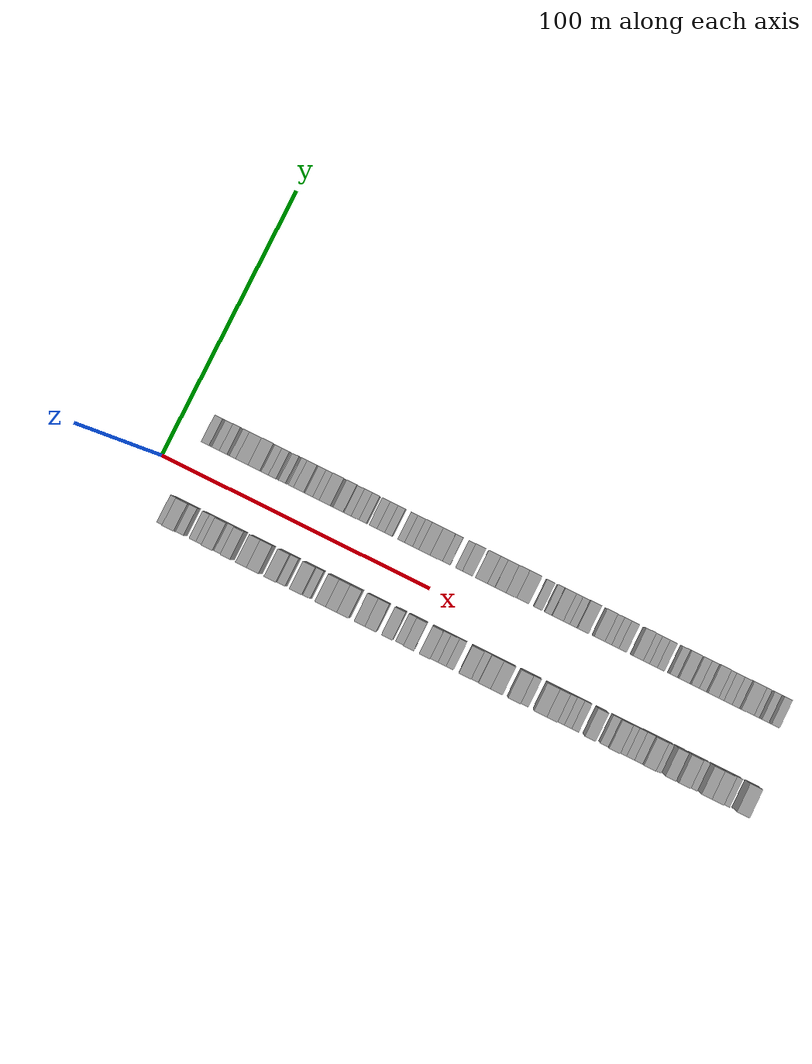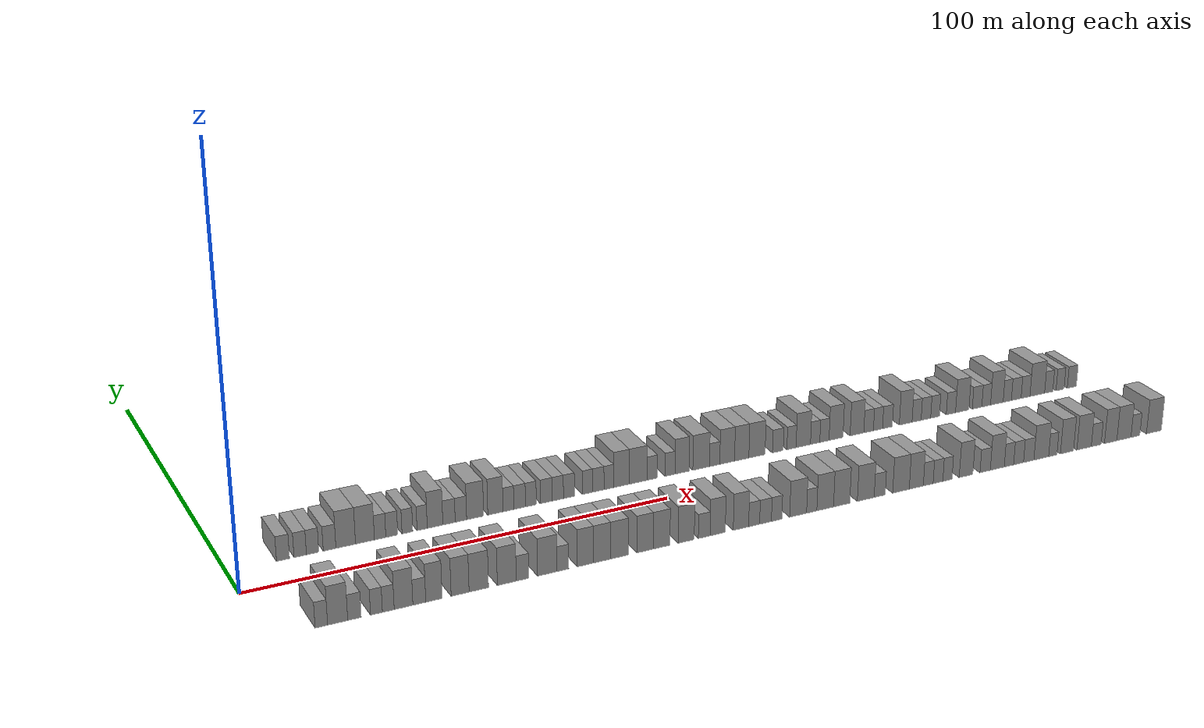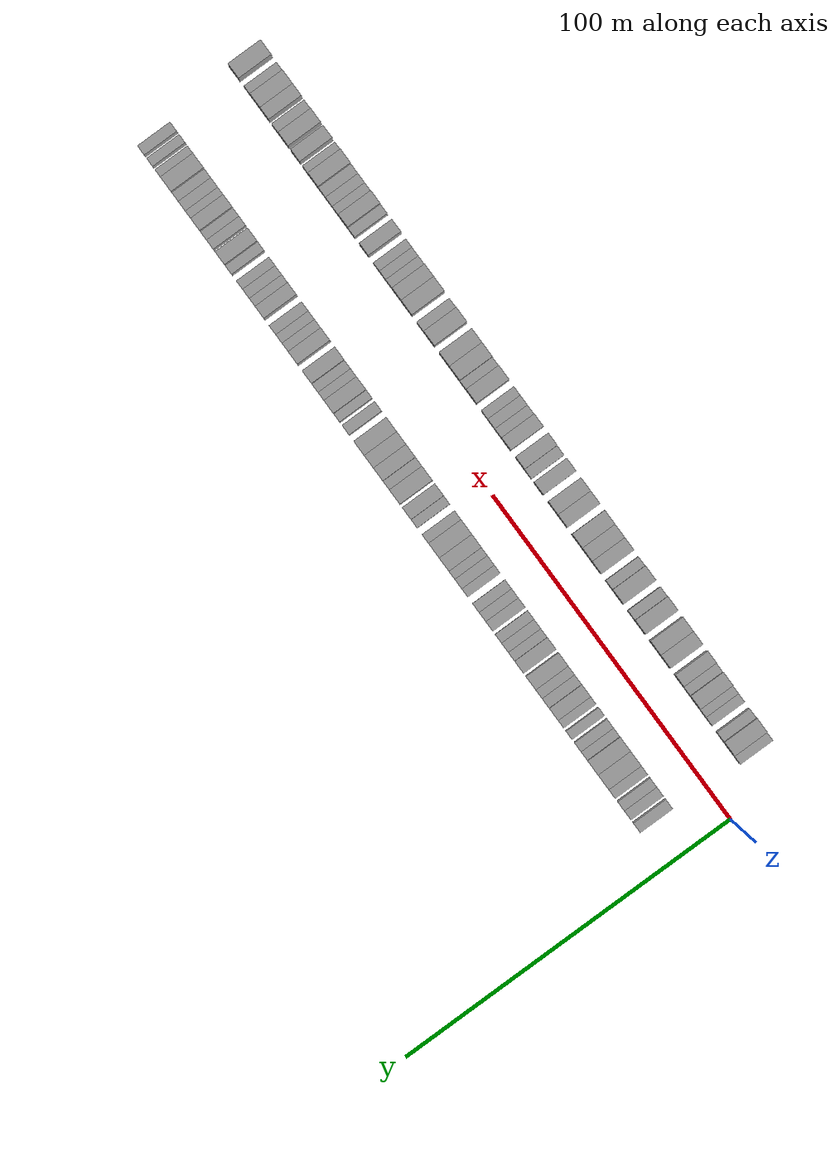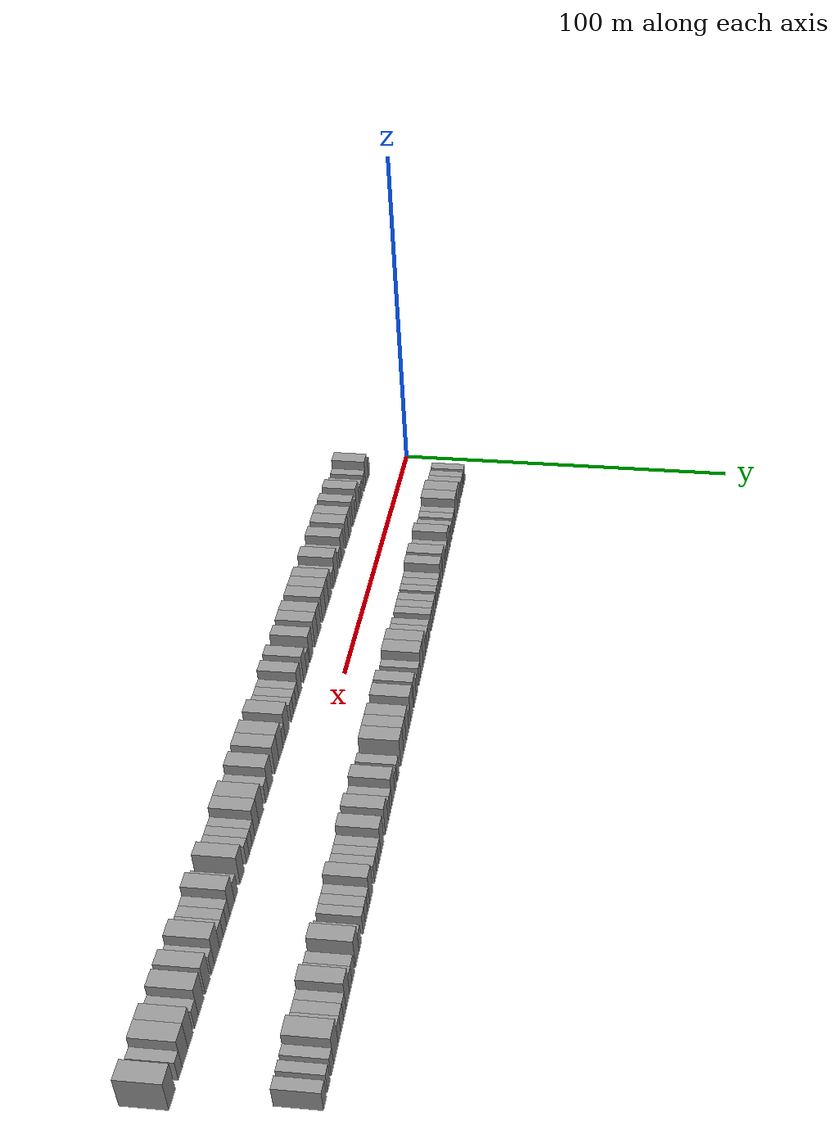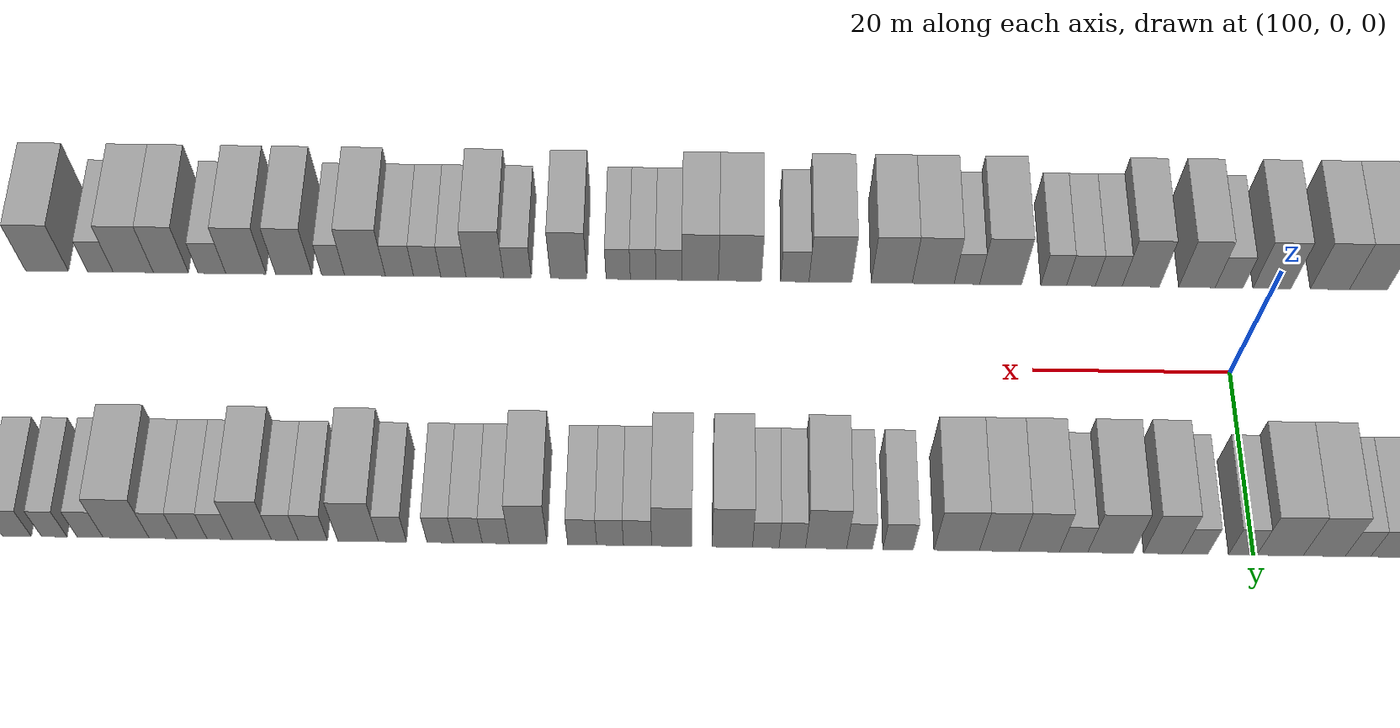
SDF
<sdf version="1.6">
 <world name="default">
  <scene>
   <sky><clouds><speed>12</speed></clouds></sky>
   <ambient>0.4 0.4 0.4 1</ambient>
   <background>0.7 0.7 0.7 1</background>
   <shadows>1</shadows>
  </scene>
  <gravity>0 0 -9.8066</gravity>
  <magnetic_field>6e-06 2.3e-05 -4.2e-05</magnetic_field>
  <physics default="0" name="default_physics" type="ode">
   <ode>
    <solver>
     <type>quick</type>
     <iters>10</iters>
     <sor>1.0</sor>
     <use_dynamic_moi_rescaling>0</use_dynamic_moi_rescaling>
    </solver>
    <constraints>
     <cfm>0</cfm>
     <erp>0.2</erp>
     <contact_max_correcting_vel>100</contact_max_correcting_vel>
     <contact_surface_layer>0.001</contact_surface_layer>
    </constraints>
   </ode>
   <max_step_size>0.004</max_step_size>
   <real_time_factor>1</real_time_factor>
   <real_time_update_rate>250</real_time_update_rate>
  </physics>
  <light name="sun" type="directional">
   <pose>0 0 10 0 0 0</pose>
   <diffuse>0.8 0.8 0.8 1</diffuse>
   <specular>0.2 0.2 0.2 1</specular>
   <attenuation>
    <range>1000</range>
    <constant>0.9</constant>
    <linear>0.01</linear>
    <quadratic>0.001</quadratic>
   </attenuation>
   <direction>-0.5 0.1 -0.9</direction>
  </light>
  <model name="building_1">
   <static>1</static>
   <pose>12.4577 15.0000 0 0.000000 0.000000 1.570796</pose>
   <link name="link">
    <pose>0 0 3.00 0 0 0</pose>
    <collision name="collision"><geometry><box><size>10.0000 2.9153 6.0000</size></box></geometry></collision>
    <visual name="visual">
     <cast_shadows>0</cast_shadows>
     <geometry><box><size>10.0000 2.9153 6.0000</size></box></geometry>
     <material>
      <script>
       <uri>model://grey_wall/materials/scripts</uri>
       <uri>model://grey_wall/materials/textures</uri>
       <name>vrc/grey_wall</name>
      </script>
     </material>
    </visual>
   </link>
  </model>
  <model name="building_2">
   <static>1</static>
   <pose>16.3046 15.0000 0 0.000000 0.000000 1.570796</pose>
   <link name="link">
    <pose>0 0 3.00 0 0 0</pose>
    <collision name="collision"><geometry><box><size>10.0000 2.7787 6.0000</size></box></geometry></collision>
    <visual name="visual">
     <cast_shadows>0</cast_shadows>
     <geometry><box><size>10.0000 2.7787 6.0000</size></box></geometry>
     <material>
      <script>
       <uri>model://grey_wall/materials/scripts</uri>
       <uri>model://grey_wall/materials/textures</uri>
       <name>vrc/grey_wall</name>
      </script>
     </material>
    </visual>
   </link>
  </model>
  <model name="building_3">
   <static>1</static>
   <pose>19.0882 15.0000 0 0.000000 0.000000 1.570796</pose>
   <link name="link">
    <pose>0 0 3.00 0 0 0</pose>
    <collision name="collision"><geometry><box><size>10.0000 2.7884 6.0000</size></box></geometry></collision>
    <visual name="visual">
     <cast_shadows>0</cast_shadows>
     <geometry><box><size>10.0000 2.7884 6.0000</size></box></geometry>
     <material>
      <script>
       <uri>model://grey_wall/materials/scripts</uri>
       <uri>model://grey_wall/materials/textures</uri>
       <name>vrc/grey_wall</name>
      </script>
     </material>
    </visual>
   </link>
  </model>
  <model name="building_4">
   <static>1</static>
   <pose>22.9180 15.0000 0 0.000000 0.000000 1.570796</pose>
   <link name="link">
    <pose>0 0 3.00 0 0 0</pose>
    <collision name="collision"><geometry><box><size>10.0000 2.8712 6.0000</size></box></geometry></collision>
    <visual name="visual">
     <cast_shadows>0</cast_shadows>
     <geometry><box><size>10.0000 2.8712 6.0000</size></box></geometry>
     <material>
      <script>
       <uri>model://grey_wall/materials/scripts</uri>
       <uri>model://grey_wall/materials/textures</uri>
       <name>vrc/grey_wall</name>
      </script>
     </material>
    </visual>
   </link>
  </model>
  <model name="building_5">
   <static>1</static>
   <pose>26.5906 15.0000 0 0.000000 0.000000 1.570796</pose>
   <link name="link">
    <pose>0 0 4.50 0 0 0</pose>
    <collision name="collision"><geometry><box><size>10.0000 4.4740 9.0000</size></box></geometry></collision>
    <visual name="visual">
     <cast_shadows>0</cast_shadows>
     <geometry><box><size>10.0000 4.4740 9.0000</size></box></geometry>
     <material>
      <script>
       <uri>model://grey_wall/materials/scripts</uri>
       <uri>model://grey_wall/materials/textures</uri>
       <name>vrc/grey_wall</name>
      </script>
     </material>
    </visual>
   </link>
  </model>
  <model name="building_6">
   <static>1</static>
   <pose>31.0061 15.0000 0 0.000000 0.000000 1.570796</pose>
   <link name="link">
    <pose>0 0 4.50 0 0 0</pose>
    <collision name="collision"><geometry><box><size>10.0000 4.3570 9.0000</size></box></geometry></collision>
    <visual name="visual">
     <cast_shadows>0</cast_shadows>
     <geometry><box><size>10.0000 4.3570 9.0000</size></box></geometry>
     <material>
      <script>
       <uri>model://grey_wall/materials/scripts</uri>
       <uri>model://grey_wall/materials/textures</uri>
       <name>vrc/grey_wall</name>
      </script>
     </material>
    </visual>
   </link>
  </model>
  <model name="building_7">
   <static>1</static>
   <pose>34.4990 15.0000 0 0.000000 0.000000 1.570796</pose>
   <link name="link">
    <pose>0 0 3.00 0 0 0</pose>
    <collision name="collision"><geometry><box><size>10.0000 2.6288 6.0000</size></box></geometry></collision>
    <visual name="visual">
     <cast_shadows>0</cast_shadows>
     <geometry><box><size>10.0000 2.6288 6.0000</size></box></geometry>
     <material>
      <script>
       <uri>model://grey_wall/materials/scripts</uri>
       <uri>model://grey_wall/materials/textures</uri>
       <name>vrc/grey_wall</name>
      </script>
     </material>
    </visual>
   </link>
  </model>
  <model name="building_8">
   <static>1</static>
   <pose>37.1985 15.0000 0 0.000000 0.000000 1.570796</pose>
   <link name="link">
    <pose>0 0 3.00 0 0 0</pose>
    <collision name="collision"><geometry><box><size>10.0000 2.7701 6.0000</size></box></geometry></collision>
    <visual name="visual">
     <cast_shadows>0</cast_shadows>
     <geometry><box><size>10.0000 2.7701 6.0000</size></box></geometry>
     <material>
      <script>
       <uri>model://grey_wall/materials/scripts</uri>
       <uri>model://grey_wall/materials/textures</uri>
       <name>vrc/grey_wall</name>
      </script>
     </material>
    </visual>
   </link>
  </model>
  <model name="building_9">
   <static>1</static>
   <pose>40.8424 15.0000 0 0.000000 0.000000 1.570796</pose>
   <link name="link">
    <pose>0 0 3.00 0 0 0</pose>
    <collision name="collision"><geometry><box><size>10.0000 2.5178 6.0000</size></box></geometry></collision>
    <visual name="visual">
     <cast_shadows>0</cast_shadows>
     <geometry><box><size>10.0000 2.5178 6.0000</size></box></geometry>
     <material>
      <script>
       <uri>model://grey_wall/materials/scripts</uri>
       <uri>model://grey_wall/materials/textures</uri>
       <name>vrc/grey_wall</name>
      </script>
     </material>
    </visual>
   </link>
  </model>
  <model name="building_10">
   <static>1</static>
   <pose>44.3051 15.0000 0 0.000000 0.000000 1.570796</pose>
   <link name="link">
    <pose>0 0 3.00 0 0 0</pose>
    <collision name="collision"><geometry><box><size>10.0000 2.4076 6.0000</size></box></geometry></collision>
    <visual name="visual">
     <cast_shadows>0</cast_shadows>
     <geometry><box><size>10.0000 2.4076 6.0000</size></box></geometry>
     <material>
      <script>
       <uri>model://grey_wall/materials/scripts</uri>
       <uri>model://grey_wall/materials/textures</uri>
       <name>vrc/grey_wall</name>
      </script>
     </material>
    </visual>
   </link>
  </model>
  <model name="building_11">
   <static>1</static>
   <pose>47.3543 15.0000 0 0.000000 0.000000 1.570796</pose>
   <link name="link">
    <pose>0 0 4.50 0 0 0</pose>
    <collision name="collision"><geometry><box><size>10.0000 3.6907 9.0000</size></box></geometry></collision>
    <visual name="visual">
     <cast_shadows>0</cast_shadows>
     <geometry><box><size>10.0000 3.6907 9.0000</size></box></geometry>
     <material>
      <script>
       <uri>model://grey_wall/materials/scripts</uri>
       <uri>model://grey_wall/materials/textures</uri>
       <name>vrc/grey_wall</name>
      </script>
     </material>
    </visual>
   </link>
  </model>
  <model name="building_12">
   <static>1</static>
   <pose>50.6692 15.0000 0 0.000000 0.000000 1.570796</pose>
   <link name="link">
    <pose>0 0 3.00 0 0 0</pose>
    <collision name="collision"><geometry><box><size>10.0000 2.9390 6.0000</size></box></geometry></collision>
    <visual name="visual">
     <cast_shadows>0</cast_shadows>
     <geometry><box><size>10.0000 2.9390 6.0000</size></box></geometry>
     <material>
      <script>
       <uri>model://grey_wall/materials/scripts</uri>
       <uri>model://grey_wall/materials/textures</uri>
       <name>vrc/grey_wall</name>
      </script>
     </material>
    </visual>
   </link>
  </model>
  <model name="building_13">
   <static>1</static>
   <pose>53.5088 15.0000 0 0.000000 0.000000 1.570796</pose>
   <link name="link">
    <pose>0 0 3.00 0 0 0</pose>
    <collision name="collision"><geometry><box><size>10.0000 2.7402 6.0000</size></box></geometry></collision>
    <visual name="visual">
     <cast_shadows>0</cast_shadows>
     <geometry><box><size>10.0000 2.7402 6.0000</size></box></geometry>
     <material>
      <script>
       <uri>model://grey_wall/materials/scripts</uri>
       <uri>model://grey_wall/materials/textures</uri>
       <name>vrc/grey_wall</name>
      </script>
     </material>
    </visual>
   </link>
  </model>
  <model name="building_14">
   <static>1</static>
   <pose>56.9188 15.0000 0 0.000000 0.000000 1.570796</pose>
   <link name="link">
    <pose>0 0 4.50 0 0 0</pose>
    <collision name="collision"><geometry><box><size>10.0000 4.0799 9.0000</size></box></geometry></collision>
    <visual name="visual">
     <cast_shadows>0</cast_shadows>
     <geometry><box><size>10.0000 4.0799 9.0000</size></box></geometry>
     <material>
      <script>
       <uri>model://grey_wall/materials/scripts</uri>
       <uri>model://grey_wall/materials/textures</uri>
       <name>vrc/grey_wall</name>
      </script>
     </material>
    </visual>
   </link>
  </model>
  <model name="building_15">
   <static>1</static>
   <pose>61.8096 15.0000 0 0.000000 0.000000 1.570796</pose>
   <link name="link">
    <pose>0 0 4.50 0 0 0</pose>
    <collision name="collision"><geometry><box><size>10.0000 3.7018 9.0000</size></box></geometry></collision>
    <visual name="visual">
     <cast_shadows>0</cast_shadows>
     <geometry><box><size>10.0000 3.7018 9.0000</size></box></geometry>
     <material>
      <script>
       <uri>model://grey_wall/materials/scripts</uri>
       <uri>model://grey_wall/materials/textures</uri>
       <name>vrc/grey_wall</name>
      </script>
     </material>
    </visual>
   </link>
  </model>
  <model name="building_16">
   <static>1</static>
   <pose>64.9770 15.0000 0 0.000000 0.000000 1.570796</pose>
   <link name="link">
    <pose>0 0 3.00 0 0 0</pose>
    <collision name="collision"><geometry><box><size>10.0000 2.6329 6.0000</size></box></geometry></collision>
    <visual name="visual">
     <cast_shadows>0</cast_shadows>
     <geometry><box><size>10.0000 2.6329 6.0000</size></box></geometry>
     <material>
      <script>
       <uri>model://grey_wall/materials/scripts</uri>
       <uri>model://grey_wall/materials/textures</uri>
       <name>vrc/grey_wall</name>
      </script>
     </material>
    </visual>
   </link>
  </model>
  <model name="building_17">
   <static>1</static>
   <pose>67.7190 15.0000 0 0.000000 0.000000 1.570796</pose>
   <link name="link">
    <pose>0 0 3.00 0 0 0</pose>
    <collision name="collision"><geometry><box><size>10.0000 2.8511 6.0000</size></box></geometry></collision>
    <visual name="visual">
     <cast_shadows>0</cast_shadows>
     <geometry><box><size>10.0000 2.8511 6.0000</size></box></geometry>
     <material>
      <script>
       <uri>model://grey_wall/materials/scripts</uri>
       <uri>model://grey_wall/materials/textures</uri>
       <name>vrc/grey_wall</name>
      </script>
     </material>
    </visual>
   </link>
  </model>
  <model name="building_18">
   <static>1</static>
   <pose>70.4726 15.0000 0 0.000000 0.000000 1.570796</pose>
   <link name="link">
    <pose>0 0 3.00 0 0 0</pose>
    <collision name="collision"><geometry><box><size>10.0000 2.6562 6.0000</size></box></geometry></collision>
    <visual name="visual">
     <cast_shadows>0</cast_shadows>
     <geometry><box><size>10.0000 2.6562 6.0000</size></box></geometry>
     <material>
      <script>
       <uri>model://grey_wall/materials/scripts</uri>
       <uri>model://grey_wall/materials/textures</uri>
       <name>vrc/grey_wall</name>
      </script>
     </material>
    </visual>
   </link>
  </model>
  <model name="building_19">
   <static>1</static>
   <pose>74.2659 15.0000 0 0.000000 0.000000 1.570796</pose>
   <link name="link">
    <pose>0 0 3.00 0 0 0</pose>
    <collision name="collision"><geometry><box><size>10.0000 2.9304 6.0000</size></box></geometry></collision>
    <visual name="visual">
     <cast_shadows>0</cast_shadows>
     <geometry><box><size>10.0000 2.9304 6.0000</size></box></geometry>
     <material>
      <script>
       <uri>model://grey_wall/materials/scripts</uri>
       <uri>model://grey_wall/materials/textures</uri>
       <name>vrc/grey_wall</name>
      </script>
     </material>
    </visual>
   </link>
  </model>
  <model name="building_20">
   <static>1</static>
   <pose>77.1341 15.0000 0 0.000000 0.000000 1.570796</pose>
   <link name="link">
    <pose>0 0 3.00 0 0 0</pose>
    <collision name="collision"><geometry><box><size>10.0000 2.8060 6.0000</size></box></geometry></collision>
    <visual name="visual">
     <cast_shadows>0</cast_shadows>
     <geometry><box><size>10.0000 2.8060 6.0000</size></box></geometry>
     <material>
      <script>
       <uri>model://grey_wall/materials/scripts</uri>
       <uri>model://grey_wall/materials/textures</uri>
       <name>vrc/grey_wall</name>
      </script>
     </material>
    </visual>
   </link>
  </model>
  <model name="building_21">
   <static>1</static>
   <pose>79.9107 15.0000 0 0.000000 0.000000 1.570796</pose>
   <link name="link">
    <pose>0 0 3.00 0 0 0</pose>
    <collision name="collision"><geometry><box><size>10.0000 2.7471 6.0000</size></box></geometry></collision>
    <visual name="visual">
     <cast_shadows>0</cast_shadows>
     <geometry><box><size>10.0000 2.7471 6.0000</size></box></geometry>
     <material>
      <script>
       <uri>model://grey_wall/materials/scripts</uri>
       <uri>model://grey_wall/materials/textures</uri>
       <name>vrc/grey_wall</name>
      </script>
     </material>
    </visual>
   </link>
  </model>
  <model name="building_22">
   <static>1</static>
   <pose>84.5346 15.0000 0 0.000000 0.000000 1.570796</pose>
   <link name="link">
    <pose>0 0 3.00 0 0 0</pose>
    <collision name="collision"><geometry><box><size>10.0000 2.5008 6.0000</size></box></geometry></collision>
    <visual name="visual">
     <cast_shadows>0</cast_shadows>
     <geometry><box><size>10.0000 2.5008 6.0000</size></box></geometry>
     <material>
      <script>
       <uri>model://grey_wall/materials/scripts</uri>
       <uri>model://grey_wall/materials/textures</uri>
       <name>vrc/grey_wall</name>
      </script>
     </material>
    </visual>
   </link>
  </model>
  <model name="building_23">
   <static>1</static>
   <pose>87.2518 15.0000 0 0.000000 0.000000 1.570796</pose>
   <link name="link">
    <pose>0 0 3.00 0 0 0</pose>
    <collision name="collision"><geometry><box><size>10.0000 2.9336 6.0000</size></box></geometry></collision>
    <visual name="visual">
     <cast_shadows>0</cast_shadows>
     <geometry><box><size>10.0000 2.9336 6.0000</size></box></geometry>
     <material>
      <script>
       <uri>model://grey_wall/materials/scripts</uri>
       <uri>model://grey_wall/materials/textures</uri>
       <name>vrc/grey_wall</name>
      </script>
     </material>
    </visual>
   </link>
  </model>
  <model name="building_24">
   <static>1</static>
   <pose>89.9448 15.0000 0 0.000000 0.000000 1.570796</pose>
   <link name="link">
    <pose>0 0 3.00 0 0 0</pose>
    <collision name="collision"><geometry><box><size>10.0000 2.4523 6.0000</size></box></geometry></collision>
    <visual name="visual">
     <cast_shadows>0</cast_shadows>
     <geometry><box><size>10.0000 2.4523 6.0000</size></box></geometry>
     <material>
      <script>
       <uri>model://grey_wall/materials/scripts</uri>
       <uri>model://grey_wall/materials/textures</uri>
       <name>vrc/grey_wall</name>
      </script>
     </material>
    </visual>
   </link>
  </model>
  <model name="building_25">
   <static>1</static>
   <pose>93.1977 15.0000 0 0.000000 0.000000 1.570796</pose>
   <link name="link">
    <pose>0 0 4.50 0 0 0</pose>
    <collision name="collision"><geometry><box><size>10.0000 4.0536 9.0000</size></box></geometry></collision>
    <visual name="visual">
     <cast_shadows>0</cast_shadows>
     <geometry><box><size>10.0000 4.0536 9.0000</size></box></geometry>
     <material>
      <script>
       <uri>model://grey_wall/materials/scripts</uri>
       <uri>model://grey_wall/materials/textures</uri>
       <name>vrc/grey_wall</name>
      </script>
     </material>
    </visual>
   </link>
  </model>
  <model name="building_26">
   <static>1</static>
   <pose>97.4699 15.0000 0 0.000000 0.000000 1.570796</pose>
   <link name="link">
    <pose>0 0 4.50 0 0 0</pose>
    <collision name="collision"><geometry><box><size>10.0000 4.4908 9.0000</size></box></geometry></collision>
    <visual name="visual">
     <cast_shadows>0</cast_shadows>
     <geometry><box><size>10.0000 4.4908 9.0000</size></box></geometry>
     <material>
      <script>
       <uri>model://grey_wall/materials/scripts</uri>
       <uri>model://grey_wall/materials/textures</uri>
       <name>vrc/grey_wall</name>
      </script>
     </material>
    </visual>
   </link>
  </model>
  <model name="building_27">
   <static>1</static>
   <pose>101.0842 15.0000 0 0.000000 0.000000 1.570796</pose>
   <link name="link">
    <pose>0 0 3.00 0 0 0</pose>
    <collision name="collision"><geometry><box><size>10.0000 2.7377 6.0000</size></box></geometry></collision>
    <visual name="visual">
     <cast_shadows>0</cast_shadows>
     <geometry><box><size>10.0000 2.7377 6.0000</size></box></geometry>
     <material>
      <script>
       <uri>model://grey_wall/materials/scripts</uri>
       <uri>model://grey_wall/materials/textures</uri>
       <name>vrc/grey_wall</name>
      </script>
     </material>
    </visual>
   </link>
  </model>
  <model name="building_28">
   <static>1</static>
   <pose>105.7235 15.0000 0 0.000000 0.000000 1.570796</pose>
   <link name="link">
    <pose>0 0 3.00 0 0 0</pose>
    <collision name="collision"><geometry><box><size>10.0000 2.5409 6.0000</size></box></geometry></collision>
    <visual name="visual">
     <cast_shadows>0</cast_shadows>
     <geometry><box><size>10.0000 2.5409 6.0000</size></box></geometry>
     <material>
      <script>
       <uri>model://grey_wall/materials/scripts</uri>
       <uri>model://grey_wall/materials/textures</uri>
       <name>vrc/grey_wall</name>
      </script>
     </material>
    </visual>
   </link>
  </model>
  <model name="building_29">
   <static>1</static>
   <pose>108.8355 15.0000 0 0.000000 0.000000 1.570796</pose>
   <link name="link">
    <pose>0 0 4.50 0 0 0</pose>
    <collision name="collision"><geometry><box><size>10.0000 3.6832 9.0000</size></box></geometry></collision>
    <visual name="visual">
     <cast_shadows>0</cast_shadows>
     <geometry><box><size>10.0000 3.6832 9.0000</size></box></geometry>
     <material>
      <script>
       <uri>model://grey_wall/materials/scripts</uri>
       <uri>model://grey_wall/materials/textures</uri>
       <name>vrc/grey_wall</name>
      </script>
     </material>
    </visual>
   </link>
  </model>
  <model name="building_30">
   <static>1</static>
   <pose>113.8813 15.0000 0 0.000000 0.000000 1.570796</pose>
   <link name="link">
    <pose>0 0 4.50 0 0 0</pose>
    <collision name="collision"><geometry><box><size>10.0000 4.4084 9.0000</size></box></geometry></collision>
    <visual name="visual">
     <cast_shadows>0</cast_shadows>
     <geometry><box><size>10.0000 4.4084 9.0000</size></box></geometry>
     <material>
      <script>
       <uri>model://grey_wall/materials/scripts</uri>
       <uri>model://grey_wall/materials/textures</uri>
       <name>vrc/grey_wall</name>
      </script>
     </material>
    </visual>
   </link>
  </model>
  <model name="building_31">
   <static>1</static>
   <pose>117.4507 15.0000 0 0.000000 0.000000 1.570796</pose>
   <link name="link">
    <pose>0 0 3.00 0 0 0</pose>
    <collision name="collision"><geometry><box><size>10.0000 2.7305 6.0000</size></box></geometry></collision>
    <visual name="visual">
     <cast_shadows>0</cast_shadows>
     <geometry><box><size>10.0000 2.7305 6.0000</size></box></geometry>
     <material>
      <script>
       <uri>model://grey_wall/materials/scripts</uri>
       <uri>model://grey_wall/materials/textures</uri>
       <name>vrc/grey_wall</name>
      </script>
     </material>
    </visual>
   </link>
  </model>
  <model name="building_32">
   <static>1</static>
   <pose>120.7867 15.0000 0 0.000000 0.000000 1.570796</pose>
   <link name="link">
    <pose>0 0 4.50 0 0 0</pose>
    <collision name="collision"><geometry><box><size>10.0000 3.9415 9.0000</size></box></geometry></collision>
    <visual name="visual">
     <cast_shadows>0</cast_shadows>
     <geometry><box><size>10.0000 3.9415 9.0000</size></box></geometry>
     <material>
      <script>
       <uri>model://grey_wall/materials/scripts</uri>
       <uri>model://grey_wall/materials/textures</uri>
       <name>vrc/grey_wall</name>
      </script>
     </material>
    </visual>
   </link>
  </model>
  <model name="building_33">
   <static>1</static>
   <pose>124.6819 15.0000 0 0.000000 0.000000 1.570796</pose>
   <link name="link">
    <pose>0 0 4.50 0 0 0</pose>
    <collision name="collision"><geometry><box><size>10.0000 3.8489 9.0000</size></box></geometry></collision>
    <visual name="visual">
     <cast_shadows>0</cast_shadows>
     <geometry><box><size>10.0000 3.8489 9.0000</size></box></geometry>
     <material>
      <script>
       <uri>model://grey_wall/materials/scripts</uri>
       <uri>model://grey_wall/materials/textures</uri>
       <name>vrc/grey_wall</name>
      </script>
     </material>
    </visual>
   </link>
  </model>
  <model name="building_34">
   <static>1</static>
   <pose>128.7969 15.0000 0 0.000000 0.000000 1.570796</pose>
   <link name="link">
    <pose>0 0 4.50 0 0 0</pose>
    <collision name="collision"><geometry><box><size>10.0000 4.3810 9.0000</size></box></geometry></collision>
    <visual name="visual">
     <cast_shadows>0</cast_shadows>
     <geometry><box><size>10.0000 4.3810 9.0000</size></box></geometry>
     <material>
      <script>
       <uri>model://grey_wall/materials/scripts</uri>
       <uri>model://grey_wall/materials/textures</uri>
       <name>vrc/grey_wall</name>
      </script>
     </material>
    </visual>
   </link>
  </model>
  <model name="building_35">
   <static>1</static>
   <pose>134.4684 15.0000 0 0.000000 0.000000 1.570796</pose>
   <link name="link">
    <pose>0 0 3.00 0 0 0</pose>
    <collision name="collision"><geometry><box><size>10.0000 2.9619 6.0000</size></box></geometry></collision>
    <visual name="visual">
     <cast_shadows>0</cast_shadows>
     <geometry><box><size>10.0000 2.9619 6.0000</size></box></geometry>
     <material>
      <script>
       <uri>model://grey_wall/materials/scripts</uri>
       <uri>model://grey_wall/materials/textures</uri>
       <name>vrc/grey_wall</name>
      </script>
     </material>
    </visual>
   </link>
  </model>
  <model name="building_36">
   <static>1</static>
   <pose>138.2059 15.0000 0 0.000000 0.000000 1.570796</pose>
   <link name="link">
    <pose>0 0 3.00 0 0 0</pose>
    <collision name="collision"><geometry><box><size>10.0000 2.5131 6.0000</size></box></geometry></collision>
    <visual name="visual">
     <cast_shadows>0</cast_shadows>
     <geometry><box><size>10.0000 2.5131 6.0000</size></box></geometry>
     <material>
      <script>
       <uri>model://grey_wall/materials/scripts</uri>
       <uri>model://grey_wall/materials/textures</uri>
       <name>vrc/grey_wall</name>
      </script>
     </material>
    </visual>
   </link>
  </model>
  <model name="building_37">
   <static>1</static>
   <pose>141.4573 15.0000 0 0.000000 0.000000 1.570796</pose>
   <link name="link">
    <pose>0 0 4.50 0 0 0</pose>
    <collision name="collision"><geometry><box><size>10.0000 3.9897 9.0000</size></box></geometry></collision>
    <visual name="visual">
     <cast_shadows>0</cast_shadows>
     <geometry><box><size>10.0000 3.9897 9.0000</size></box></geometry>
     <material>
      <script>
       <uri>model://grey_wall/materials/scripts</uri>
       <uri>model://grey_wall/materials/textures</uri>
       <name>vrc/grey_wall</name>
      </script>
     </material>
    </visual>
   </link>
  </model>
  <model name="building_38">
   <static>1</static>
   <pose>144.7372 15.0000 0 0.000000 0.000000 1.570796</pose>
   <link name="link">
    <pose>0 0 3.00 0 0 0</pose>
    <collision name="collision"><geometry><box><size>10.0000 2.5700 6.0000</size></box></geometry></collision>
    <visual name="visual">
     <cast_shadows>0</cast_shadows>
     <geometry><box><size>10.0000 2.5700 6.0000</size></box></geometry>
     <material>
      <script>
       <uri>model://grey_wall/materials/scripts</uri>
       <uri>model://grey_wall/materials/textures</uri>
       <name>vrc/grey_wall</name>
      </script>
     </material>
    </visual>
   </link>
  </model>
  <model name="building_39">
   <static>1</static>
   <pose>147.3090 15.0000 0 0.000000 0.000000 1.570796</pose>
   <link name="link">
    <pose>0 0 3.00 0 0 0</pose>
    <collision name="collision"><geometry><box><size>10.0000 2.5736 6.0000</size></box></geometry></collision>
    <visual name="visual">
     <cast_shadows>0</cast_shadows>
     <geometry><box><size>10.0000 2.5736 6.0000</size></box></geometry>
     <material>
      <script>
       <uri>model://grey_wall/materials/scripts</uri>
       <uri>model://grey_wall/materials/textures</uri>
       <name>vrc/grey_wall</name>
      </script>
     </material>
    </visual>
   </link>
  </model>
  <model name="building_40">
   <static>1</static>
   <pose>150.5536 15.0000 0 0.000000 0.000000 1.570796</pose>
   <link name="link">
    <pose>0 0 4.50 0 0 0</pose>
    <collision name="collision"><geometry><box><size>10.0000 3.9157 9.0000</size></box></geometry></collision>
    <visual name="visual">
     <cast_shadows>0</cast_shadows>
     <geometry><box><size>10.0000 3.9157 9.0000</size></box></geometry>
     <material>
      <script>
       <uri>model://grey_wall/materials/scripts</uri>
       <uri>model://grey_wall/materials/textures</uri>
       <name>vrc/grey_wall</name>
      </script>
     </material>
    </visual>
   </link>
  </model>
  <model name="building_41">
   <static>1</static>
   <pose>156.4536 15.0000 0 0.000000 0.000000 1.570796</pose>
   <link name="link">
    <pose>0 0 4.50 0 0 0</pose>
    <collision name="collision"><geometry><box><size>10.0000 3.8843 9.0000</size></box></geometry></collision>
    <visual name="visual">
     <cast_shadows>0</cast_shadows>
     <geometry><box><size>10.0000 3.8843 9.0000</size></box></geometry>
     <material>
      <script>
       <uri>model://grey_wall/materials/scripts</uri>
       <uri>model://grey_wall/materials/textures</uri>
       <name>vrc/grey_wall</name>
      </script>
     </material>
    </visual>
   </link>
  </model>
  <model name="building_42">
   <static>1</static>
   <pose>159.7617 15.0000 0 0.000000 0.000000 1.570796</pose>
   <link name="link">
    <pose>0 0 3.00 0 0 0</pose>
    <collision name="collision"><geometry><box><size>10.0000 2.7318 6.0000</size></box></geometry></collision>
    <visual name="visual">
     <cast_shadows>0</cast_shadows>
     <geometry><box><size>10.0000 2.7318 6.0000</size></box></geometry>
     <material>
      <script>
       <uri>model://grey_wall/materials/scripts</uri>
       <uri>model://grey_wall/materials/textures</uri>
       <name>vrc/grey_wall</name>
      </script>
     </material>
    </visual>
   </link>
  </model>
  <model name="building_43">
   <static>1</static>
   <pose>162.4258 15.0000 0 0.000000 0.000000 1.570796</pose>
   <link name="link">
    <pose>0 0 3.00 0 0 0</pose>
    <collision name="collision"><geometry><box><size>10.0000 2.5965 6.0000</size></box></geometry></collision>
    <visual name="visual">
     <cast_shadows>0</cast_shadows>
     <geometry><box><size>10.0000 2.5965 6.0000</size></box></geometry>
     <material>
      <script>
       <uri>model://grey_wall/materials/scripts</uri>
       <uri>model://grey_wall/materials/textures</uri>
       <name>vrc/grey_wall</name>
      </script>
     </material>
    </visual>
   </link>
  </model>
  <model name="building_44">
   <static>1</static>
   <pose>165.1306 15.0000 0 0.000000 0.000000 1.570796</pose>
   <link name="link">
    <pose>0 0 3.00 0 0 0</pose>
    <collision name="collision"><geometry><box><size>10.0000 2.8132 6.0000</size></box></geometry></collision>
    <visual name="visual">
     <cast_shadows>0</cast_shadows>
     <geometry><box><size>10.0000 2.8132 6.0000</size></box></geometry>
     <material>
      <script>
       <uri>model://grey_wall/materials/scripts</uri>
       <uri>model://grey_wall/materials/textures</uri>
       <name>vrc/grey_wall</name>
      </script>
     </material>
    </visual>
   </link>
  </model>
  <model name="building_45">
   <static>1</static>
   <pose>170.3809 15.0000 0 0.000000 0.000000 1.570796</pose>
   <link name="link">
    <pose>0 0 4.50 0 0 0</pose>
    <collision name="collision"><geometry><box><size>10.0000 3.6875 9.0000</size></box></geometry></collision>
    <visual name="visual">
     <cast_shadows>0</cast_shadows>
     <geometry><box><size>10.0000 3.6875 9.0000</size></box></geometry>
     <material>
      <script>
       <uri>model://grey_wall/materials/scripts</uri>
       <uri>model://grey_wall/materials/textures</uri>
       <name>vrc/grey_wall</name>
      </script>
     </material>
    </visual>
   </link>
  </model>
  <model name="building_46">
   <static>1</static>
   <pose>173.5392 15.0000 0 0.000000 0.000000 1.570796</pose>
   <link name="link">
    <pose>0 0 3.00 0 0 0</pose>
    <collision name="collision"><geometry><box><size>10.0000 2.6291 6.0000</size></box></geometry></collision>
    <visual name="visual">
     <cast_shadows>0</cast_shadows>
     <geometry><box><size>10.0000 2.6291 6.0000</size></box></geometry>
     <material>
      <script>
       <uri>model://grey_wall/materials/scripts</uri>
       <uri>model://grey_wall/materials/textures</uri>
       <name>vrc/grey_wall</name>
      </script>
     </material>
    </visual>
   </link>
  </model>
  <model name="building_47">
   <static>1</static>
   <pose>176.2488 15.0000 0 0.000000 0.000000 1.570796</pose>
   <link name="link">
    <pose>0 0 3.00 0 0 0</pose>
    <collision name="collision"><geometry><box><size>10.0000 2.7902 6.0000</size></box></geometry></collision>
    <visual name="visual">
     <cast_shadows>0</cast_shadows>
     <geometry><box><size>10.0000 2.7902 6.0000</size></box></geometry>
     <material>
      <script>
       <uri>model://grey_wall/materials/scripts</uri>
       <uri>model://grey_wall/materials/textures</uri>
       <name>vrc/grey_wall</name>
      </script>
     </material>
    </visual>
   </link>
  </model>
  <model name="building_48">
   <static>1</static>
   <pose>178.9324 15.0000 0 0.000000 0.000000 1.570796</pose>
   <link name="link">
    <pose>0 0 3.00 0 0 0</pose>
    <collision name="collision"><geometry><box><size>10.0000 2.5769 6.0000</size></box></geometry></collision>
    <visual name="visual">
     <cast_shadows>0</cast_shadows>
     <geometry><box><size>10.0000 2.5769 6.0000</size></box></geometry>
     <material>
      <script>
       <uri>model://grey_wall/materials/scripts</uri>
       <uri>model://grey_wall/materials/textures</uri>
       <name>vrc/grey_wall</name>
      </script>
     </material>
    </visual>
   </link>
  </model>
  <model name="building_49">
   <static>1</static>
   <pose>183.5829 15.0000 0 0.000000 0.000000 1.570796</pose>
   <link name="link">
    <pose>0 0 3.00 0 0 0</pose>
    <collision name="collision"><geometry><box><size>10.0000 2.7243 6.0000</size></box></geometry></collision>
    <visual name="visual">
     <cast_shadows>0</cast_shadows>
     <geometry><box><size>10.0000 2.7243 6.0000</size></box></geometry>
     <material>
      <script>
       <uri>model://grey_wall/materials/scripts</uri>
       <uri>model://grey_wall/materials/textures</uri>
       <name>vrc/grey_wall</name>
      </script>
     </material>
    </visual>
   </link>
  </model>
  <model name="building_50">
   <static>1</static>
   <pose>186.9273 15.0000 0 0.000000 0.000000 1.570796</pose>
   <link name="link">
    <pose>0 0 4.50 0 0 0</pose>
    <collision name="collision"><geometry><box><size>10.0000 3.9645 9.0000</size></box></geometry></collision>
    <visual name="visual">
     <cast_shadows>0</cast_shadows>
     <geometry><box><size>10.0000 3.9645 9.0000</size></box></geometry>
     <material>
      <script>
       <uri>model://grey_wall/materials/scripts</uri>
       <uri>model://grey_wall/materials/textures</uri>
       <name>vrc/grey_wall</name>
      </script>
     </material>
    </visual>
   </link>
  </model>
  <model name="building_51">
   <static>1</static>
   <pose>191.3352 15.0000 0 0.000000 0.000000 1.570796</pose>
   <link name="link">
    <pose>0 0 3.00 0 0 0</pose>
    <collision name="collision"><geometry><box><size>10.0000 2.8514 6.0000</size></box></geometry></collision>
    <visual name="visual">
     <cast_shadows>0</cast_shadows>
     <geometry><box><size>10.0000 2.8514 6.0000</size></box></geometry>
     <material>
      <script>
       <uri>model://grey_wall/materials/scripts</uri>
       <uri>model://grey_wall/materials/textures</uri>
       <name>vrc/grey_wall</name>
      </script>
     </material>
    </visual>
   </link>
  </model>
  <model name="building_52">
   <static>1</static>
   <pose>194.0658 15.0000 0 0.000000 0.000000 1.570796</pose>
   <link name="link">
    <pose>0 0 3.00 0 0 0</pose>
    <collision name="collision"><geometry><box><size>10.0000 2.6098 6.0000</size></box></geometry></collision>
    <visual name="visual">
     <cast_shadows>0</cast_shadows>
     <geometry><box><size>10.0000 2.6098 6.0000</size></box></geometry>
     <material>
      <script>
       <uri>model://grey_wall/materials/scripts</uri>
       <uri>model://grey_wall/materials/textures</uri>
       <name>vrc/grey_wall</name>
      </script>
     </material>
    </visual>
   </link>
  </model>
  <model name="building_53">
   <static>1</static>
   <pose>197.2658 15.0000 0 0.000000 0.000000 1.570796</pose>
   <link name="link">
    <pose>0 0 4.50 0 0 0</pose>
    <collision name="collision"><geometry><box><size>10.0000 3.7900 9.0000</size></box></geometry></collision>
    <visual name="visual">
     <cast_shadows>0</cast_shadows>
     <geometry><box><size>10.0000 3.7900 9.0000</size></box></geometry>
     <material>
      <script>
       <uri>model://grey_wall/materials/scripts</uri>
       <uri>model://grey_wall/materials/textures</uri>
       <name>vrc/grey_wall</name>
      </script>
     </material>
    </visual>
   </link>
  </model>
  <model name="building_54">
   <static>1</static>
   <pose>200.4045 15.0000 0 0.000000 0.000000 1.570796</pose>
   <link name="link">
    <pose>0 0 3.00 0 0 0</pose>
    <collision name="collision"><geometry><box><size>10.0000 2.4874 6.0000</size></box></geometry></collision>
    <visual name="visual">
     <cast_shadows>0</cast_shadows>
     <geometry><box><size>10.0000 2.4874 6.0000</size></box></geometry>
     <material>
      <script>
       <uri>model://grey_wall/materials/scripts</uri>
       <uri>model://grey_wall/materials/textures</uri>
       <name>vrc/grey_wall</name>
      </script>
     </material>
    </visual>
   </link>
  </model>
  <model name="building_55">
   <static>1</static>
   <pose>203.1226 15.0000 0 0.000000 0.000000 1.570796</pose>
   <link name="link">
    <pose>0 0 3.00 0 0 0</pose>
    <collision name="collision"><geometry><box><size>10.0000 2.9488 6.0000</size></box></geometry></collision>
    <visual name="visual">
     <cast_shadows>0</cast_shadows>
     <geometry><box><size>10.0000 2.9488 6.0000</size></box></geometry>
     <material>
      <script>
       <uri>model://grey_wall/materials/scripts</uri>
       <uri>model://grey_wall/materials/textures</uri>
       <name>vrc/grey_wall</name>
      </script>
     </material>
    </visual>
   </link>
  </model>
  <model name="building_56">
   <static>1</static>
   <pose>205.9491 15.0000 0 0.000000 0.000000 1.570796</pose>
   <link name="link">
    <pose>0 0 3.00 0 0 0</pose>
    <collision name="collision"><geometry><box><size>10.0000 2.7042 6.0000</size></box></geometry></collision>
    <visual name="visual">
     <cast_shadows>0</cast_shadows>
     <geometry><box><size>10.0000 2.7042 6.0000</size></box></geometry>
     <material>
      <script>
       <uri>model://grey_wall/materials/scripts</uri>
       <uri>model://grey_wall/materials/textures</uri>
       <name>vrc/grey_wall</name>
      </script>
     </material>
    </visual>
   </link>
  </model>
  <model name="building_57">
   <static>1</static>
   <pose>209.5503 15.0000 0 0.000000 0.000000 1.570796</pose>
   <link name="link">
    <pose>0 0 4.50 0 0 0</pose>
    <collision name="collision"><geometry><box><size>10.0000 4.4981 9.0000</size></box></geometry></collision>
    <visual name="visual">
     <cast_shadows>0</cast_shadows>
     <geometry><box><size>10.0000 4.4981 9.0000</size></box></geometry>
     <material>
      <script>
       <uri>model://grey_wall/materials/scripts</uri>
       <uri>model://grey_wall/materials/textures</uri>
       <name>vrc/grey_wall</name>
      </script>
     </material>
    </visual>
   </link>
  </model>
  <model name="building_58">
   <static>1</static>
   <pose>213.0587 15.0000 0 0.000000 0.000000 1.570796</pose>
   <link name="link">
    <pose>0 0 3.00 0 0 0</pose>
    <collision name="collision"><geometry><box><size>10.0000 2.5187 6.0000</size></box></geometry></collision>
    <visual name="visual">
     <cast_shadows>0</cast_shadows>
     <geometry><box><size>10.0000 2.5187 6.0000</size></box></geometry>
     <material>
      <script>
       <uri>model://grey_wall/materials/scripts</uri>
       <uri>model://grey_wall/materials/textures</uri>
       <name>vrc/grey_wall</name>
      </script>
     </material>
    </visual>
   </link>
  </model>
  <model name="building_59">
   <static>1</static>
   <pose>216.5635 15.0000 0 0.000000 0.000000 1.570796</pose>
   <link name="link">
    <pose>0 0 3.00 0 0 0</pose>
    <collision name="collision"><geometry><box><size>10.0000 2.4909 6.0000</size></box></geometry></collision>
    <visual name="visual">
     <cast_shadows>0</cast_shadows>
     <geometry><box><size>10.0000 2.4909 6.0000</size></box></geometry>
     <material>
      <script>
       <uri>model://grey_wall/materials/scripts</uri>
       <uri>model://grey_wall/materials/textures</uri>
       <name>vrc/grey_wall</name>
      </script>
     </material>
    </visual>
   </link>
  </model>
  <model name="building_60">
   <static>1</static>
   <pose>220.2247 15.0000 0 0.000000 0.000000 1.570796</pose>
   <link name="link">
    <pose>0 0 3.00 0 0 0</pose>
    <collision name="collision"><geometry><box><size>10.0000 2.8314 6.0000</size></box></geometry></collision>
    <visual name="visual">
     <cast_shadows>0</cast_shadows>
     <geometry><box><size>10.0000 2.8314 6.0000</size></box></geometry>
     <material>
      <script>
       <uri>model://grey_wall/materials/scripts</uri>
       <uri>model://grey_wall/materials/textures</uri>
       <name>vrc/grey_wall</name>
      </script>
     </material>
    </visual>
   </link>
  </model>
  <model name="building_61">
   <static>1</static>
   <pose>11.3222 -15.0000 0 0.000000 0.000000 1.570796</pose>
   <link name="link">
    <pose>0 0 3.00 0 0 0</pose>
    <collision name="collision"><geometry><box><size>10.0000 2.6444 6.0000</size></box></geometry></collision>
    <visual name="visual">
     <cast_shadows>0</cast_shadows>
     <geometry><box><size>10.0000 2.6444 6.0000</size></box></geometry>
     <material>
      <script>
       <uri>model://grey_wall/materials/scripts</uri>
       <uri>model://grey_wall/materials/textures</uri>
       <name>vrc/grey_wall</name>
      </script>
     </material>
    </visual>
   </link>
  </model>
  <model name="building_62">
   <static>1</static>
   <pose>14.7861 -15.0000 0 0.000000 0.000000 1.570796</pose>
   <link name="link">
    <pose>0 0 4.50 0 0 0</pose>
    <collision name="collision"><geometry><box><size>10.0000 4.2834 9.0000</size></box></geometry></collision>
    <visual name="visual">
     <cast_shadows>0</cast_shadows>
     <geometry><box><size>10.0000 4.2834 9.0000</size></box></geometry>
     <material>
      <script>
       <uri>model://grey_wall/materials/scripts</uri>
       <uri>model://grey_wall/materials/textures</uri>
       <name>vrc/grey_wall</name>
      </script>
     </material>
    </visual>
   </link>
  </model>
  <model name="building_63">
   <static>1</static>
   <pose>18.3802 -15.0000 0 0.000000 0.000000 1.570796</pose>
   <link name="link">
    <pose>0 0 3.00 0 0 0</pose>
    <collision name="collision"><geometry><box><size>10.0000 2.9049 6.0000</size></box></geometry></collision>
    <visual name="visual">
     <cast_shadows>0</cast_shadows>
     <geometry><box><size>10.0000 2.9049 6.0000</size></box></geometry>
     <material>
      <script>
       <uri>model://grey_wall/materials/scripts</uri>
       <uri>model://grey_wall/materials/textures</uri>
       <name>vrc/grey_wall</name>
      </script>
     </material>
    </visual>
   </link>
  </model>
  <model name="building_64">
   <static>1</static>
   <pose>23.1178 -15.0000 0 0.000000 0.000000 1.570796</pose>
   <link name="link">
    <pose>0 0 3.00 0 0 0</pose>
    <collision name="collision"><geometry><box><size>10.0000 2.5702 6.0000</size></box></geometry></collision>
    <visual name="visual">
     <cast_shadows>0</cast_shadows>
     <geometry><box><size>10.0000 2.5702 6.0000</size></box></geometry>
     <material>
      <script>
       <uri>model://grey_wall/materials/scripts</uri>
       <uri>model://grey_wall/materials/textures</uri>
       <name>vrc/grey_wall</name>
      </script>
     </material>
    </visual>
   </link>
  </model>
  <model name="building_65">
   <static>1</static>
   <pose>25.6850 -15.0000 0 0.000000 0.000000 1.570796</pose>
   <link name="link">
    <pose>0 0 3.00 0 0 0</pose>
    <collision name="collision"><geometry><box><size>10.0000 2.5643 6.0000</size></box></geometry></collision>
    <visual name="visual">
     <cast_shadows>0</cast_shadows>
     <geometry><box><size>10.0000 2.5643 6.0000</size></box></geometry>
     <material>
      <script>
       <uri>model://grey_wall/materials/scripts</uri>
       <uri>model://grey_wall/materials/textures</uri>
       <name>vrc/grey_wall</name>
      </script>
     </material>
    </visual>
   </link>
  </model>
  <model name="building_66">
   <static>1</static>
   <pose>29.0117 -15.0000 0 0.000000 0.000000 1.570796</pose>
   <link name="link">
    <pose>0 0 4.50 0 0 0</pose>
    <collision name="collision"><geometry><box><size>10.0000 4.0891 9.0000</size></box></geometry></collision>
    <visual name="visual">
     <cast_shadows>0</cast_shadows>
     <geometry><box><size>10.0000 4.0891 9.0000</size></box></geometry>
     <material>
      <script>
       <uri>model://grey_wall/materials/scripts</uri>
       <uri>model://grey_wall/materials/textures</uri>
       <name>vrc/grey_wall</name>
      </script>
     </material>
    </visual>
   </link>
  </model>
  <model name="building_67">
   <static>1</static>
   <pose>32.4728 -15.0000 0 0.000000 0.000000 1.570796</pose>
   <link name="link">
    <pose>0 0 3.00 0 0 0</pose>
    <collision name="collision"><geometry><box><size>10.0000 2.8331 6.0000</size></box></geometry></collision>
    <visual name="visual">
     <cast_shadows>0</cast_shadows>
     <geometry><box><size>10.0000 2.8331 6.0000</size></box></geometry>
     <material>
      <script>
       <uri>model://grey_wall/materials/scripts</uri>
       <uri>model://grey_wall/materials/textures</uri>
       <name>vrc/grey_wall</name>
      </script>
     </material>
    </visual>
   </link>
  </model>
  <model name="building_68">
   <static>1</static>
   <pose>35.7061 -15.0000 0 0.000000 0.000000 1.570796</pose>
   <link name="link">
    <pose>0 0 4.50 0 0 0</pose>
    <collision name="collision"><geometry><box><size>10.0000 3.6334 9.0000</size></box></geometry></collision>
    <visual name="visual">
     <cast_shadows>0</cast_shadows>
     <geometry><box><size>10.0000 3.6334 9.0000</size></box></geometry>
     <material>
      <script>
       <uri>model://grey_wall/materials/scripts</uri>
       <uri>model://grey_wall/materials/textures</uri>
       <name>vrc/grey_wall</name>
      </script>
     </material>
    </visual>
   </link>
  </model>
  <model name="building_69">
   <static>1</static>
   <pose>41.5302 -15.0000 0 0.000000 0.000000 1.570796</pose>
   <link name="link">
    <pose>0 0 4.50 0 0 0</pose>
    <collision name="collision"><geometry><box><size>10.0000 4.0148 9.0000</size></box></geometry></collision>
    <visual name="visual">
     <cast_shadows>0</cast_shadows>
     <geometry><box><size>10.0000 4.0148 9.0000</size></box></geometry>
     <material>
      <script>
       <uri>model://grey_wall/materials/scripts</uri>
       <uri>model://grey_wall/materials/textures</uri>
       <name>vrc/grey_wall</name>
      </script>
     </material>
    </visual>
   </link>
  </model>
  <model name="building_70">
   <static>1</static>
   <pose>45.7287 -15.0000 0 0.000000 0.000000 1.570796</pose>
   <link name="link">
    <pose>0 0 4.50 0 0 0</pose>
    <collision name="collision"><geometry><box><size>10.0000 4.3823 9.0000</size></box></geometry></collision>
    <visual name="visual">
     <cast_shadows>0</cast_shadows>
     <geometry><box><size>10.0000 4.3823 9.0000</size></box></geometry>
     <material>
      <script>
       <uri>model://grey_wall/materials/scripts</uri>
       <uri>model://grey_wall/materials/textures</uri>
       <name>vrc/grey_wall</name>
      </script>
     </material>
    </visual>
   </link>
  </model>
  <model name="building_71">
   <static>1</static>
   <pose>52.0782 -15.0000 0 0.000000 0.000000 1.570796</pose>
   <link name="link">
    <pose>0 0 4.50 0 0 0</pose>
    <collision name="collision"><geometry><box><size>10.0000 4.3167 9.0000</size></box></geometry></collision>
    <visual name="visual">
     <cast_shadows>0</cast_shadows>
     <geometry><box><size>10.0000 4.3167 9.0000</size></box></geometry>
     <material>
      <script>
       <uri>model://grey_wall/materials/scripts</uri>
       <uri>model://grey_wall/materials/textures</uri>
       <name>vrc/grey_wall</name>
      </script>
     </material>
    </visual>
   </link>
  </model>
  <model name="building_72">
   <static>1</static>
   <pose>55.6879 -15.0000 0 0.000000 0.000000 1.570796</pose>
   <link name="link">
    <pose>0 0 3.00 0 0 0</pose>
    <collision name="collision"><geometry><box><size>10.0000 2.9027 6.0000</size></box></geometry></collision>
    <visual name="visual">
     <cast_shadows>0</cast_shadows>
     <geometry><box><size>10.0000 2.9027 6.0000</size></box></geometry>
     <material>
      <script>
       <uri>model://grey_wall/materials/scripts</uri>
       <uri>model://grey_wall/materials/textures</uri>
       <name>vrc/grey_wall</name>
      </script>
     </material>
    </visual>
   </link>
  </model>
  <model name="building_73">
   <static>1</static>
   <pose>61.3761 -15.0000 0 0.000000 0.000000 1.570796</pose>
   <link name="link">
    <pose>0 0 4.50 0 0 0</pose>
    <collision name="collision"><geometry><box><size>10.0000 4.4735 9.0000</size></box></geometry></collision>
    <visual name="visual">
     <cast_shadows>0</cast_shadows>
     <geometry><box><size>10.0000 4.4735 9.0000</size></box></geometry>
     <material>
      <script>
       <uri>model://grey_wall/materials/scripts</uri>
       <uri>model://grey_wall/materials/textures</uri>
       <name>vrc/grey_wall</name>
      </script>
     </material>
    </visual>
   </link>
  </model>
  <model name="building_74">
   <static>1</static>
   <pose>65.0046 -15.0000 0 0.000000 0.000000 1.570796</pose>
   <link name="link">
    <pose>0 0 3.00 0 0 0</pose>
    <collision name="collision"><geometry><box><size>10.0000 2.7834 6.0000</size></box></geometry></collision>
    <visual name="visual">
     <cast_shadows>0</cast_shadows>
     <geometry><box><size>10.0000 2.7834 6.0000</size></box></geometry>
     <material>
      <script>
       <uri>model://grey_wall/materials/scripts</uri>
       <uri>model://grey_wall/materials/textures</uri>
       <name>vrc/grey_wall</name>
      </script>
     </material>
    </visual>
   </link>
  </model>
  <model name="building_75">
   <static>1</static>
   <pose>70.3221 -15.0000 0 0.000000 0.000000 1.570796</pose>
   <link name="link">
    <pose>0 0 4.50 0 0 0</pose>
    <collision name="collision"><geometry><box><size>10.0000 3.8517 9.0000</size></box></geometry></collision>
    <visual name="visual">
     <cast_shadows>0</cast_shadows>
     <geometry><box><size>10.0000 3.8517 9.0000</size></box></geometry>
     <material>
      <script>
       <uri>model://grey_wall/materials/scripts</uri>
       <uri>model://grey_wall/materials/textures</uri>
       <name>vrc/grey_wall</name>
      </script>
     </material>
    </visual>
   </link>
  </model>
  <model name="building_76">
   <static>1</static>
   <pose>74.2866 -15.0000 0 0.000000 0.000000 1.570796</pose>
   <link name="link">
    <pose>0 0 4.50 0 0 0</pose>
    <collision name="collision"><geometry><box><size>10.0000 4.0773 9.0000</size></box></geometry></collision>
    <visual name="visual">
     <cast_shadows>0</cast_shadows>
     <geometry><box><size>10.0000 4.0773 9.0000</size></box></geometry>
     <material>
      <script>
       <uri>model://grey_wall/materials/scripts</uri>
       <uri>model://grey_wall/materials/textures</uri>
       <name>vrc/grey_wall</name>
      </script>
     </material>
    </visual>
   </link>
  </model>
  <model name="building_77">
   <static>1</static>
   <pose>78.4624 -15.0000 0 0.000000 0.000000 1.570796</pose>
   <link name="link">
    <pose>0 0 4.50 0 0 0</pose>
    <collision name="collision"><geometry><box><size>10.0000 4.2743 9.0000</size></box></geometry></collision>
    <visual name="visual">
     <cast_shadows>0</cast_shadows>
     <geometry><box><size>10.0000 4.2743 9.0000</size></box></geometry>
     <material>
      <script>
       <uri>model://grey_wall/materials/scripts</uri>
       <uri>model://grey_wall/materials/textures</uri>
       <name>vrc/grey_wall</name>
      </script>
     </material>
    </visual>
   </link>
  </model>
  <model name="building_78">
   <static>1</static>
   <pose>84.5637 -15.0000 0 0.000000 0.000000 1.570796</pose>
   <link name="link">
    <pose>0 0 4.50 0 0 0</pose>
    <collision name="collision"><geometry><box><size>10.0000 3.9282 9.0000</size></box></geometry></collision>
    <visual name="visual">
     <cast_shadows>0</cast_shadows>
     <geometry><box><size>10.0000 3.9282 9.0000</size></box></geometry>
     <material>
      <script>
       <uri>model://grey_wall/materials/scripts</uri>
       <uri>model://grey_wall/materials/textures</uri>
       <name>vrc/grey_wall</name>
      </script>
     </material>
    </visual>
   </link>
  </model>
  <model name="building_79">
   <static>1</static>
   <pose>88.5553 -15.0000 0 0.000000 0.000000 1.570796</pose>
   <link name="link">
    <pose>0 0 4.50 0 0 0</pose>
    <collision name="collision"><geometry><box><size>10.0000 4.0551 9.0000</size></box></geometry></collision>
    <visual name="visual">
     <cast_shadows>0</cast_shadows>
     <geometry><box><size>10.0000 4.0551 9.0000</size></box></geometry>
     <material>
      <script>
       <uri>model://grey_wall/materials/scripts</uri>
       <uri>model://grey_wall/materials/textures</uri>
       <name>vrc/grey_wall</name>
      </script>
     </material>
    </visual>
   </link>
  </model>
  <model name="building_80">
   <static>1</static>
   <pose>94.5588 -15.0000 0 0.000000 0.000000 1.570796</pose>
   <link name="link">
    <pose>0 0 4.50 0 0 0</pose>
    <collision name="collision"><geometry><box><size>10.0000 3.9518 9.0000</size></box></geometry></collision>
    <visual name="visual">
     <cast_shadows>0</cast_shadows>
     <geometry><box><size>10.0000 3.9518 9.0000</size></box></geometry>
     <material>
      <script>
       <uri>model://grey_wall/materials/scripts</uri>
       <uri>model://grey_wall/materials/textures</uri>
       <name>vrc/grey_wall</name>
      </script>
     </material>
    </visual>
   </link>
  </model>
  <model name="building_81">
   <static>1</static>
   <pose>98.9947 -15.0000 0 0.000000 0.000000 1.570796</pose>
   <link name="link">
    <pose>0 0 3.00 0 0 0</pose>
    <collision name="collision"><geometry><box><size>10.0000 2.9199 6.0000</size></box></geometry></collision>
    <visual name="visual">
     <cast_shadows>0</cast_shadows>
     <geometry><box><size>10.0000 2.9199 6.0000</size></box></geometry>
     <material>
      <script>
       <uri>model://grey_wall/materials/scripts</uri>
       <uri>model://grey_wall/materials/textures</uri>
       <name>vrc/grey_wall</name>
      </script>
     </material>
    </visual>
   </link>
  </model>
  <model name="building_82">
   <static>1</static>
   <pose>102.3497 -15.0000 0 0.000000 0.000000 1.570796</pose>
   <link name="link">
    <pose>0 0 4.50 0 0 0</pose>
    <collision name="collision"><geometry><box><size>10.0000 3.7901 9.0000</size></box></geometry></collision>
    <visual name="visual">
     <cast_shadows>0</cast_shadows>
     <geometry><box><size>10.0000 3.7901 9.0000</size></box></geometry>
     <material>
      <script>
       <uri>model://grey_wall/materials/scripts</uri>
       <uri>model://grey_wall/materials/textures</uri>
       <name>vrc/grey_wall</name>
      </script>
     </material>
    </visual>
   </link>
  </model>
  <model name="building_83">
   <static>1</static>
   <pose>108.1817 -15.0000 0 0.000000 0.000000 1.570796</pose>
   <link name="link">
    <pose>0 0 4.50 0 0 0</pose>
    <collision name="collision"><geometry><box><size>10.0000 3.8739 9.0000</size></box></geometry></collision>
    <visual name="visual">
     <cast_shadows>0</cast_shadows>
     <geometry><box><size>10.0000 3.8739 9.0000</size></box></geometry>
     <material>
      <script>
       <uri>model://grey_wall/materials/scripts</uri>
       <uri>model://grey_wall/materials/textures</uri>
       <name>vrc/grey_wall</name>
      </script>
     </material>
    </visual>
   </link>
  </model>
  <model name="building_84">
   <static>1</static>
   <pose>111.5092 -15.0000 0 0.000000 0.000000 1.570796</pose>
   <link name="link">
    <pose>0 0 3.00 0 0 0</pose>
    <collision name="collision"><geometry><box><size>10.0000 2.7813 6.0000</size></box></geometry></collision>
    <visual name="visual">
     <cast_shadows>0</cast_shadows>
     <geometry><box><size>10.0000 2.7813 6.0000</size></box></geometry>
     <material>
      <script>
       <uri>model://grey_wall/materials/scripts</uri>
       <uri>model://grey_wall/materials/textures</uri>
       <name>vrc/grey_wall</name>
      </script>
     </material>
    </visual>
   </link>
  </model>
  <model name="building_85">
   <static>1</static>
   <pose>114.3971 -15.0000 0 0.000000 0.000000 1.570796</pose>
   <link name="link">
    <pose>0 0 3.00 0 0 0</pose>
    <collision name="collision"><geometry><box><size>10.0000 2.9945 6.0000</size></box></geometry></collision>
    <visual name="visual">
     <cast_shadows>0</cast_shadows>
     <geometry><box><size>10.0000 2.9945 6.0000</size></box></geometry>
     <material>
      <script>
       <uri>model://grey_wall/materials/scripts</uri>
       <uri>model://grey_wall/materials/textures</uri>
       <name>vrc/grey_wall</name>
      </script>
     </material>
    </visual>
   </link>
  </model>
  <model name="building_86">
   <static>1</static>
   <pose>117.2305 -15.0000 0 0.000000 0.000000 1.570796</pose>
   <link name="link">
    <pose>0 0 3.00 0 0 0</pose>
    <collision name="collision"><geometry><box><size>10.0000 2.6723 6.0000</size></box></geometry></collision>
    <visual name="visual">
     <cast_shadows>0</cast_shadows>
     <geometry><box><size>10.0000 2.6723 6.0000</size></box></geometry>
     <material>
      <script>
       <uri>model://grey_wall/materials/scripts</uri>
       <uri>model://grey_wall/materials/textures</uri>
       <name>vrc/grey_wall</name>
      </script>
     </material>
    </visual>
   </link>
  </model>
  <model name="building_87">
   <static>1</static>
   <pose>122.7505 -15.0000 0 0.000000 0.000000 1.570796</pose>
   <link name="link">
    <pose>0 0 4.50 0 0 0</pose>
    <collision name="collision"><geometry><box><size>10.0000 4.3677 9.0000</size></box></geometry></collision>
    <visual name="visual">
     <cast_shadows>0</cast_shadows>
     <geometry><box><size>10.0000 4.3677 9.0000</size></box></geometry>
     <material>
      <script>
       <uri>model://grey_wall/materials/scripts</uri>
       <uri>model://grey_wall/materials/textures</uri>
       <name>vrc/grey_wall</name>
      </script>
     </material>
    </visual>
   </link>
  </model>
  <model name="building_88">
   <static>1</static>
   <pose>126.2627 -15.0000 0 0.000000 0.000000 1.570796</pose>
   <link name="link">
    <pose>0 0 3.00 0 0 0</pose>
    <collision name="collision"><geometry><box><size>10.0000 2.6568 6.0000</size></box></geometry></collision>
    <visual name="visual">
     <cast_shadows>0</cast_shadows>
     <geometry><box><size>10.0000 2.6568 6.0000</size></box></geometry>
     <material>
      <script>
       <uri>model://grey_wall/materials/scripts</uri>
       <uri>model://grey_wall/materials/textures</uri>
       <name>vrc/grey_wall</name>
      </script>
     </material>
    </visual>
   </link>
  </model>
  <model name="building_89">
   <static>1</static>
   <pose>129.7688 -15.0000 0 0.000000 0.000000 1.570796</pose>
   <link name="link">
    <pose>0 0 4.50 0 0 0</pose>
    <collision name="collision"><geometry><box><size>10.0000 4.3553 9.0000</size></box></geometry></collision>
    <visual name="visual">
     <cast_shadows>0</cast_shadows>
     <geometry><box><size>10.0000 4.3553 9.0000</size></box></geometry>
     <material>
      <script>
       <uri>model://grey_wall/materials/scripts</uri>
       <uri>model://grey_wall/materials/textures</uri>
       <name>vrc/grey_wall</name>
      </script>
     </material>
    </visual>
   </link>
  </model>
  <model name="building_90">
   <static>1</static>
   <pose>134.0827 -15.0000 0 0.000000 0.000000 1.570796</pose>
   <link name="link">
    <pose>0 0 4.50 0 0 0</pose>
    <collision name="collision"><geometry><box><size>10.0000 4.2727 9.0000</size></box></geometry></collision>
    <visual name="visual">
     <cast_shadows>0</cast_shadows>
     <geometry><box><size>10.0000 4.2727 9.0000</size></box></geometry>
     <material>
      <script>
       <uri>model://grey_wall/materials/scripts</uri>
       <uri>model://grey_wall/materials/textures</uri>
       <name>vrc/grey_wall</name>
      </script>
     </material>
    </visual>
   </link>
  </model>
  <model name="building_91">
   <static>1</static>
   <pose>140.4590 -15.0000 0 0.000000 0.000000 1.570796</pose>
   <link name="link">
    <pose>0 0 4.50 0 0 0</pose>
    <collision name="collision"><geometry><box><size>10.0000 4.4799 9.0000</size></box></geometry></collision>
    <visual name="visual">
     <cast_shadows>0</cast_shadows>
     <geometry><box><size>10.0000 4.4799 9.0000</size></box></geometry>
     <material>
      <script>
       <uri>model://grey_wall/materials/scripts</uri>
       <uri>model://grey_wall/materials/textures</uri>
       <name>vrc/grey_wall</name>
      </script>
     </material>
    </visual>
   </link>
  </model>
  <model name="building_92">
   <static>1</static>
   <pose>144.1731 -15.0000 0 0.000000 0.000000 1.570796</pose>
   <link name="link">
    <pose>0 0 3.00 0 0 0</pose>
    <collision name="collision"><geometry><box><size>10.0000 2.9483 6.0000</size></box></geometry></collision>
    <visual name="visual">
     <cast_shadows>0</cast_shadows>
     <geometry><box><size>10.0000 2.9483 6.0000</size></box></geometry>
     <material>
      <script>
       <uri>model://grey_wall/materials/scripts</uri>
       <uri>model://grey_wall/materials/textures</uri>
       <name>vrc/grey_wall</name>
      </script>
     </material>
    </visual>
   </link>
  </model>
  <model name="building_93">
   <static>1</static>
   <pose>149.8913 -15.0000 0 0.000000 0.000000 1.570796</pose>
   <link name="link">
    <pose>0 0 4.50 0 0 0</pose>
    <collision name="collision"><geometry><box><size>10.0000 4.4880 9.0000</size></box></geometry></collision>
    <visual name="visual">
     <cast_shadows>0</cast_shadows>
     <geometry><box><size>10.0000 4.4880 9.0000</size></box></geometry>
     <material>
      <script>
       <uri>model://grey_wall/materials/scripts</uri>
       <uri>model://grey_wall/materials/textures</uri>
       <name>vrc/grey_wall</name>
      </script>
     </material>
    </visual>
   </link>
  </model>
  <model name="building_94">
   <static>1</static>
   <pose>154.0439 -15.0000 0 0.000000 0.000000 1.570796</pose>
   <link name="link">
    <pose>0 0 4.50 0 0 0</pose>
    <collision name="collision"><geometry><box><size>10.0000 3.8172 9.0000</size></box></geometry></collision>
    <visual name="visual">
     <cast_shadows>0</cast_shadows>
     <geometry><box><size>10.0000 3.8172 9.0000</size></box></geometry>
     <material>
      <script>
       <uri>model://grey_wall/materials/scripts</uri>
       <uri>model://grey_wall/materials/textures</uri>
       <name>vrc/grey_wall</name>
      </script>
     </material>
    </visual>
   </link>
  </model>
  <model name="building_95">
   <static>1</static>
   <pose>157.2957 -15.0000 0 0.000000 0.000000 1.570796</pose>
   <link name="link">
    <pose>0 0 3.00 0 0 0</pose>
    <collision name="collision"><geometry><box><size>10.0000 2.6863 6.0000</size></box></geometry></collision>
    <visual name="visual">
     <cast_shadows>0</cast_shadows>
     <geometry><box><size>10.0000 2.6863 6.0000</size></box></geometry>
     <material>
      <script>
       <uri>model://grey_wall/materials/scripts</uri>
       <uri>model://grey_wall/materials/textures</uri>
       <name>vrc/grey_wall</name>
      </script>
     </material>
    </visual>
   </link>
  </model>
  <model name="building_96">
   <static>1</static>
   <pose>159.9669 -15.0000 0 0.000000 0.000000 1.570796</pose>
   <link name="link">
    <pose>0 0 3.00 0 0 0</pose>
    <collision name="collision"><geometry><box><size>10.0000 2.6561 6.0000</size></box></geometry></collision>
    <visual name="visual">
     <cast_shadows>0</cast_shadows>
     <geometry><box><size>10.0000 2.6561 6.0000</size></box></geometry>
     <material>
      <script>
       <uri>model://grey_wall/materials/scripts</uri>
       <uri>model://grey_wall/materials/textures</uri>
       <name>vrc/grey_wall</name>
      </script>
     </material>
    </visual>
   </link>
  </model>
  <model name="building_97">
   <static>1</static>
   <pose>162.5588 -15.0000 0 0.000000 0.000000 1.570796</pose>
   <link name="link">
    <pose>0 0 3.00 0 0 0</pose>
    <collision name="collision"><geometry><box><size>10.0000 2.5278 6.0000</size></box></geometry></collision>
    <visual name="visual">
     <cast_shadows>0</cast_shadows>
     <geometry><box><size>10.0000 2.5278 6.0000</size></box></geometry>
     <material>
      <script>
       <uri>model://grey_wall/materials/scripts</uri>
       <uri>model://grey_wall/materials/textures</uri>
       <name>vrc/grey_wall</name>
      </script>
     </material>
    </visual>
   </link>
  </model>
  <model name="building_98">
   <static>1</static>
   <pose>167.7188 -15.0000 0 0.000000 0.000000 1.570796</pose>
   <link name="link">
    <pose>0 0 4.50 0 0 0</pose>
    <collision name="collision"><geometry><box><size>10.0000 3.7923 9.0000</size></box></geometry></collision>
    <visual name="visual">
     <cast_shadows>0</cast_shadows>
     <geometry><box><size>10.0000 3.7923 9.0000</size></box></geometry>
     <material>
      <script>
       <uri>model://grey_wall/materials/scripts</uri>
       <uri>model://grey_wall/materials/textures</uri>
       <name>vrc/grey_wall</name>
      </script>
     </material>
    </visual>
   </link>
  </model>
  <model name="building_99">
   <static>1</static>
   <pose>173.0561 -15.0000 0 0.000000 0.000000 1.570796</pose>
   <link name="link">
    <pose>0 0 3.00 0 0 0</pose>
    <collision name="collision"><geometry><box><size>10.0000 2.8822 6.0000</size></box></geometry></collision>
    <visual name="visual">
     <cast_shadows>0</cast_shadows>
     <geometry><box><size>10.0000 2.8822 6.0000</size></box></geometry>
     <material>
      <script>
       <uri>model://grey_wall/materials/scripts</uri>
       <uri>model://grey_wall/materials/textures</uri>
       <name>vrc/grey_wall</name>
      </script>
     </material>
    </visual>
   </link>
  </model>
  <model name="building_100">
   <static>1</static>
   <pose>176.4670 -15.0000 0 0.000000 0.000000 1.570796</pose>
   <link name="link">
    <pose>0 0 4.50 0 0 0</pose>
    <collision name="collision"><geometry><box><size>10.0000 3.9397 9.0000</size></box></geometry></collision>
    <visual name="visual">
     <cast_shadows>0</cast_shadows>
     <geometry><box><size>10.0000 3.9397 9.0000</size></box></geometry>
     <material>
      <script>
       <uri>model://grey_wall/materials/scripts</uri>
       <uri>model://grey_wall/materials/textures</uri>
       <name>vrc/grey_wall</name>
      </script>
     </material>
    </visual>
   </link>
  </model>
  <model name="building_101">
   <static>1</static>
   <pose>179.7580 -15.0000 0 0.000000 0.000000 1.570796</pose>
   <link name="link">
    <pose>0 0 3.00 0 0 0</pose>
    <collision name="collision"><geometry><box><size>10.0000 2.6423 6.0000</size></box></geometry></collision>
    <visual name="visual">
     <cast_shadows>0</cast_shadows>
     <geometry><box><size>10.0000 2.6423 6.0000</size></box></geometry>
     <material>
      <script>
       <uri>model://grey_wall/materials/scripts</uri>
       <uri>model://grey_wall/materials/textures</uri>
       <name>vrc/grey_wall</name>
      </script>
     </material>
    </visual>
   </link>
  </model>
  <model name="building_102">
   <static>1</static>
   <pose>182.4958 -15.0000 0 0.000000 0.000000 1.570796</pose>
   <link name="link">
    <pose>0 0 3.00 0 0 0</pose>
    <collision name="collision"><geometry><box><size>10.0000 2.8333 6.0000</size></box></geometry></collision>
    <visual name="visual">
     <cast_shadows>0</cast_shadows>
     <geometry><box><size>10.0000 2.8333 6.0000</size></box></geometry>
     <material>
      <script>
       <uri>model://grey_wall/materials/scripts</uri>
       <uri>model://grey_wall/materials/textures</uri>
       <name>vrc/grey_wall</name>
      </script>
     </material>
    </visual>
   </link>
  </model>
  <model name="building_103">
   <static>1</static>
   <pose>185.3948 -15.0000 0 0.000000 0.000000 1.570796</pose>
   <link name="link">
    <pose>0 0 3.00 0 0 0</pose>
    <collision name="collision"><geometry><box><size>10.0000 2.9648 6.0000</size></box></geometry></collision>
    <visual name="visual">
     <cast_shadows>0</cast_shadows>
     <geometry><box><size>10.0000 2.9648 6.0000</size></box></geometry>
     <material>
      <script>
       <uri>model://grey_wall/materials/scripts</uri>
       <uri>model://grey_wall/materials/textures</uri>
       <name>vrc/grey_wall</name>
      </script>
     </material>
    </visual>
   </link>
  </model>
  <model name="building_104">
   <static>1</static>
   <pose>188.9987 -15.0000 0 0.000000 0.000000 1.570796</pose>
   <link name="link">
    <pose>0 0 4.50 0 0 0</pose>
    <collision name="collision"><geometry><box><size>10.0000 4.2431 9.0000</size></box></geometry></collision>
    <visual name="visual">
     <cast_shadows>0</cast_shadows>
     <geometry><box><size>10.0000 4.2431 9.0000</size></box></geometry>
     <material>
      <script>
       <uri>model://grey_wall/materials/scripts</uri>
       <uri>model://grey_wall/materials/textures</uri>
       <name>vrc/grey_wall</name>
      </script>
     </material>
    </visual>
   </link>
  </model>
  <model name="building_105">
   <static>1</static>
   <pose>192.3229 -15.0000 0 0.000000 0.000000 1.570796</pose>
   <link name="link">
    <pose>0 0 3.00 0 0 0</pose>
    <collision name="collision"><geometry><box><size>10.0000 2.4051 6.0000</size></box></geometry></collision>
    <visual name="visual">
     <cast_shadows>0</cast_shadows>
     <geometry><box><size>10.0000 2.4051 6.0000</size></box></geometry>
     <material>
      <script>
       <uri>model://grey_wall/materials/scripts</uri>
       <uri>model://grey_wall/materials/textures</uri>
       <name>vrc/grey_wall</name>
      </script>
     </material>
    </visual>
   </link>
  </model>
  <model name="building_106">
   <static>1</static>
   <pose>196.4271 -15.0000 0 0.000000 0.000000 1.570796</pose>
   <link name="link">
    <pose>0 0 4.50 0 0 0</pose>
    <collision name="collision"><geometry><box><size>10.0000 3.8033 9.0000</size></box></geometry></collision>
    <visual name="visual">
     <cast_shadows>0</cast_shadows>
     <geometry><box><size>10.0000 3.8033 9.0000</size></box></geometry>
     <material>
      <script>
       <uri>model://grey_wall/materials/scripts</uri>
       <uri>model://grey_wall/materials/textures</uri>
       <name>vrc/grey_wall</name>
      </script>
     </material>
    </visual>
   </link>
  </model>
  <model name="building_107">
   <static>1</static>
   <pose>201.4361 -15.0000 0 0.000000 0.000000 1.570796</pose>
   <link name="link">
    <pose>0 0 4.50 0 0 0</pose>
    <collision name="collision"><geometry><box><size>10.0000 4.2147 9.0000</size></box></geometry></collision>
    <visual name="visual">
     <cast_shadows>0</cast_shadows>
     <geometry><box><size>10.0000 4.2147 9.0000</size></box></geometry>
     <material>
      <script>
       <uri>model://grey_wall/materials/scripts</uri>
       <uri>model://grey_wall/materials/textures</uri>
       <name>vrc/grey_wall</name>
      </script>
     </material>
    </visual>
   </link>
  </model>
  <model name="building_108">
   <static>1</static>
   <pose>204.9939 -15.0000 0 0.000000 0.000000 1.570796</pose>
   <link name="link">
    <pose>0 0 3.00 0 0 0</pose>
    <collision name="collision"><geometry><box><size>10.0000 2.9010 6.0000</size></box></geometry></collision>
    <visual name="visual">
     <cast_shadows>0</cast_shadows>
     <geometry><box><size>10.0000 2.9010 6.0000</size></box></geometry>
     <material>
      <script>
       <uri>model://grey_wall/materials/scripts</uri>
       <uri>model://grey_wall/materials/textures</uri>
       <name>vrc/grey_wall</name>
      </script>
     </material>
    </visual>
   </link>
  </model>
  <model name="building_109">
   <static>1</static>
   <pose>209.2825 -15.0000 0 0.000000 0.000000 1.570796</pose>
   <link name="link">
    <pose>0 0 4.50 0 0 0</pose>
    <collision name="collision"><geometry><box><size>10.0000 3.6761 9.0000</size></box></geometry></collision>
    <visual name="visual">
     <cast_shadows>0</cast_shadows>
     <geometry><box><size>10.0000 3.6761 9.0000</size></box></geometry>
     <material>
      <script>
       <uri>model://grey_wall/materials/scripts</uri>
       <uri>model://grey_wall/materials/textures</uri>
       <name>vrc/grey_wall</name>
      </script>
     </material>
    </visual>
   </link>
  </model>
  <model name="building_110">
   <static>1</static>
   <pose>213.2285 -15.0000 0 0.000000 0.000000 1.570796</pose>
   <link name="link">
    <pose>0 0 4.50 0 0 0</pose>
    <collision name="collision"><geometry><box><size>10.0000 4.2161 9.0000</size></box></geometry></collision>
    <visual name="visual">
     <cast_shadows>0</cast_shadows>
     <geometry><box><size>10.0000 4.2161 9.0000</size></box></geometry>
     <material>
      <script>
       <uri>model://grey_wall/materials/scripts</uri>
       <uri>model://grey_wall/materials/textures</uri>
       <name>vrc/grey_wall</name>
      </script>
     </material>
    </visual>
   </link>
  </model>
  <model name="building_111">
   <static>1</static>
   <pose>216.6727 -15.0000 0 0.000000 0.000000 1.570796</pose>
   <link name="link">
    <pose>0 0 3.00 0 0 0</pose>
    <collision name="collision"><geometry><box><size>10.0000 2.6724 6.0000</size></box></geometry></collision>
    <visual name="visual">
     <cast_shadows>0</cast_shadows>
     <geometry><box><size>10.0000 2.6724 6.0000</size></box></geometry>
     <material>
      <script>
       <uri>model://grey_wall/materials/scripts</uri>
       <uri>model://grey_wall/materials/textures</uri>
       <name>vrc/grey_wall</name>
      </script>
     </material>
    </visual>
   </link>
  </model>
  <model name="building_112">
   <static>1</static>
   <pose>222.2518 -15.0000 0 0.000000 0.000000 1.570796</pose>
   <link name="link">
    <pose>0 0 4.50 0 0 0</pose>
    <collision name="collision"><geometry><box><size>10.0000 4.4858 9.0000</size></box></geometry></collision>
    <visual name="visual">
     <cast_shadows>0</cast_shadows>
     <geometry><box><size>10.0000 4.4858 9.0000</size></box></geometry>
     <material>
      <script>
       <uri>model://grey_wall/materials/scripts</uri>
       <uri>model://grey_wall/materials/textures</uri>
       <name>vrc/grey_wall</name>
      </script>
     </material>
    </visual>
   </link>
  </model>
 </world>
</sdf>
